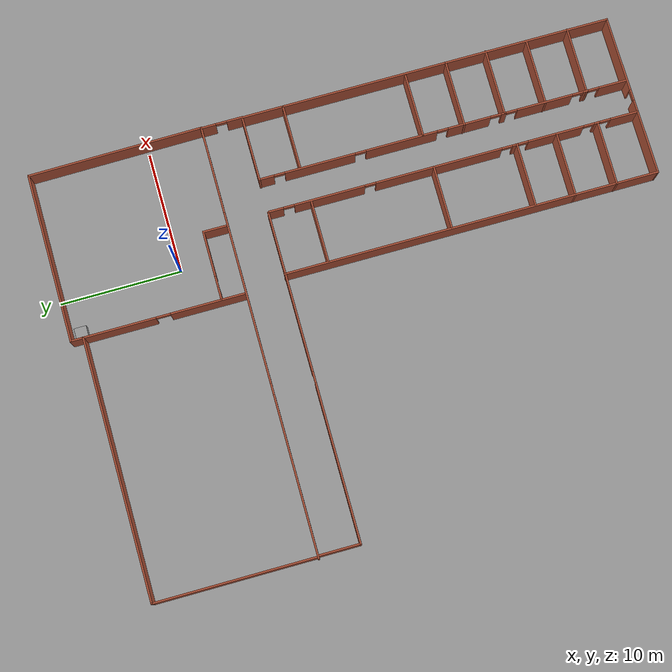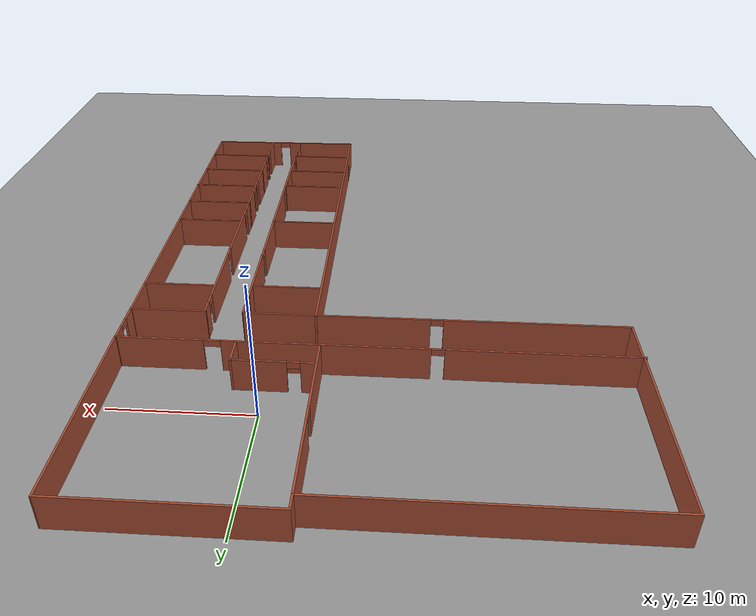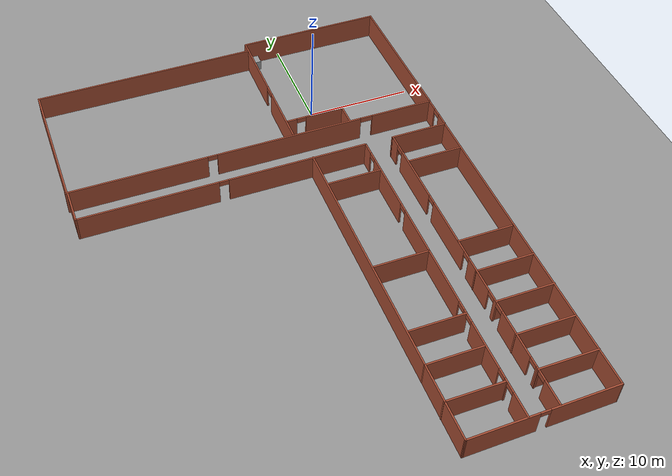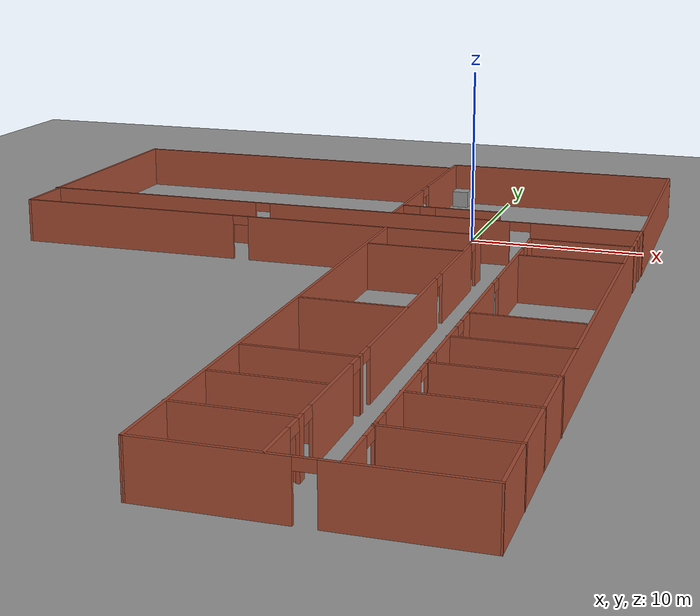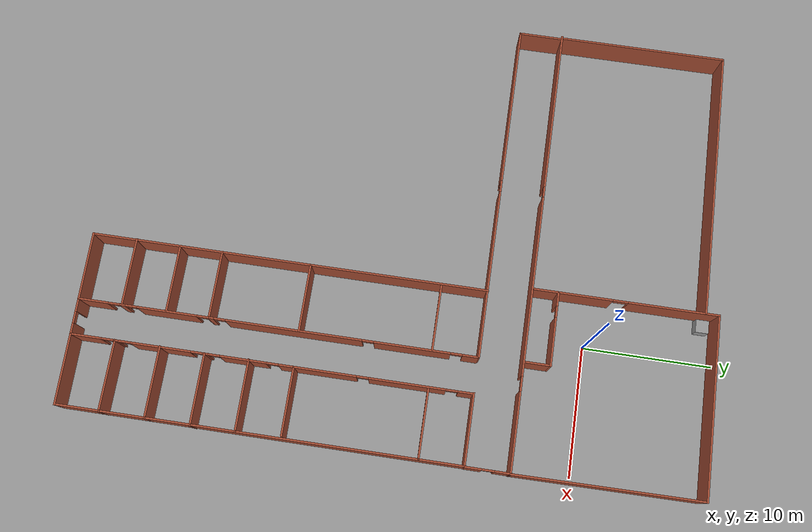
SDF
<?xml version="1.0" ?>
<sdf version='1.7'>
  <model name='fapsmap.obj'>
    <light name='sun' type='directional'>
      <cast_shadows>1</cast_shadows>
      <pose>0 0 10 0 -0 0</pose>
      <diffuse>0.8 0.8 0.8 1</diffuse>
      <specular>0.2 0.2 0.2 1</specular>
      <attenuation>
        <range>1000</range>
        <constant>0.9</constant>
        <linear>0.01</linear>
        <quadratic>0.001</quadratic>
      </attenuation>
      <direction>-0.5 0.1 -0.9</direction>
      <spot>
        <inner_angle>0</inner_angle>
        <outer_angle>0</outer_angle>
        <falloff>0</falloff>
      </spot>
    </light>
    <model name='ground_plane'>
      <static>1</static>
      <link name='link'>
        <collision name='collision'>
          <geometry>
            <plane>
              <normal>0 0 1</normal>
              <size>100 100</size>
            </plane>
          </geometry>
          <surface>
            <friction>
              <ode>
                <mu>100</mu>
                <mu2>50</mu2>
              </ode>
              <torsional>
                <ode/>
              </torsional>
            </friction>
            <contact>
              <ode/>
            </contact>
            <bounce/>
          </surface>
          <max_contacts>10</max_contacts>
        </collision>
        <visual name='visual'>
          <cast_shadows>0</cast_shadows>
          <geometry>
            <plane>
              <normal>0 0 1</normal>
              <size>100 100</size>
            </plane>
          </geometry>
          <material>
            <script>
              <uri>file://media/materials/scripts/gazebo.material</uri>
              <name>Gazebo/Grey</name>
            </script>
          </material>
        </visual>
        <self_collide>0</self_collide>
        <enable_wind>0</enable_wind>
        <kinematic>0</kinematic>
      </link>
    </model>
    <gravity>0 0 -9.8</gravity>
    <magnetic_field>6e-06 2.3e-05 -4.2e-05</magnetic_field>
    <atmosphere type='adiabatic'/>
    <physics type='ode'>
      <max_step_size>0.001</max_step_size>
      <real_time_factor>1</real_time_factor>
      <real_time_update_rate>1000</real_time_update_rate>
    </physics>
    <scene>
      <ambient>0.4 0.4 0.4 1</ambient>
      <background>0.7 0.7 0.7 1</background>
      <shadows>1</shadows>
    </scene>
    <audio>
      <device>default</device>
    </audio>
    <wind/>
    <spherical_coordinates>
      <surface_model>EARTH_WGS84</surface_model>
      <latitude_deg>0</latitude_deg>
      <longitude_deg>0</longitude_deg>
      <elevation>0</elevation>
      <heading_deg>0</heading_deg>
    </spherical_coordinates>
    <model name='fapsmap.obj'>
      <pose>-7.30116 -14.55 0 0 -0 0</pose>
      <link name='Wall_20'>
        <pose>-0.000299 9.9725 0 0 -0 3.1403</pose>
        <visual name='Wall_20_Visual_0'>
          <pose>-14.7424 0 1.25 0 -0 0</pose>
          <geometry>
            <box>
              <size>6.13838 0.15 2.5</size>
            </box>
          </geometry>
          <material>
            <script>
              <uri>file://media/materials/scripts/gazebo.material</uri>
              <name>Gazebo/Bricks</name>
            </script>
            <ambient>1 1 1 1</ambient>
          </material>
          <meta>
            <layer>0</layer>
          </meta>
        </visual>
        <collision name='Wall_20_Collision_0'>
          <geometry>
            <box>
              <size>6.13838 0.15 2.5</size>
            </box>
          </geometry>
          <pose>-14.7424 0 1.25 0 -0 0</pose>
          <max_contacts>10</max_contacts>
          <surface>
            <contact>
              <ode/>
            </contact>
            <bounce/>
            <friction>
              <torsional>
                <ode/>
              </torsional>
              <ode/>
            </friction>
          </surface>
        </collision>
        <visual name='Wall_20_Visual_1'>
          <pose>-3.4046 0 1.25 0 -0 0</pose>
          <geometry>
            <box>
              <size>14.2081 0.15 2.5</size>
            </box>
          </geometry>
          <material>
            <script>
              <uri>file://media/materials/scripts/gazebo.material</uri>
              <name>Gazebo/Bricks</name>
            </script>
            <ambient>1 1 1 1</ambient>
          </material>
          <meta>
            <layer>0</layer>
          </meta>
        </visual>
        <collision name='Wall_20_Collision_1'>
          <geometry>
            <box>
              <size>14.2081 0.15 2.5</size>
            </box>
          </geometry>
          <pose>-3.4046 0 1.25 0 -0 0</pose>
          <max_contacts>10</max_contacts>
          <surface>
            <contact>
              <ode/>
            </contact>
            <bounce/>
            <friction>
              <torsional>
                <ode/>
              </torsional>
              <ode/>
            </friction>
          </surface>
        </collision>
        <visual name='Wall_20_Visual_2'>
          <pose>11.2055 0 1.25 0 -0 0</pose>
          <geometry>
            <box>
              <size>13.2121 0.15 2.5</size>
            </box>
          </geometry>
          <material>
            <script>
              <uri>file://media/materials/scripts/gazebo.material</uri>
              <name>Gazebo/Bricks</name>
            </script>
            <ambient>1 1 1 1</ambient>
          </material>
          <meta>
            <layer>0</layer>gazebo /Home/faps/building_editor_models/fapsmap.obj

          </meta>
        </visual>
        <collision name='Wall_20_Collision_2'>
          <geometry>
            <box>
              <size>13.2121 0.15 2.5</size>
            </box>
          </geometry>
          <pose>11.2055 0 1.25 0 -0 0</pose>
          <max_contacts>10</max_contacts>
          <surface>
            <contact>
              <ode/>
            </contact>
            <bounce/>
            <friction>
              <torsional>
                <ode/>
              </torsional>
              <ode/>
            </friction>
          </surface>
        </collision>
        <visual name='Wall_20_Visual_3'>
          <pose>-11.0909 0 2.25 0 -0 0</pose>
          <geometry>
            <box>
              <size>1.16451 0.15 0.5</size>
            </box>
          </geometry>
          <material>
            <script>
              <uri>file://media/materials/scripts/gazebo.material</uri>
              <name>Gazebo/Bricks</name>
            </script>
            <ambient>1 1 1 1</ambient>
          </material>
          <meta>
            <layer>0</layer>
          </meta>
        </visual>
        <collision name='Wall_20_Collision_3'>
          <geometry>
            <box>
              <size>1.16451 0.15 0.5</size>
            </box>
          </geometry>
          <pose>-11.0909 0 2.25 0 -0 0</pose>
          <max_contacts>10</max_contacts>
          <surface>
            <contact>
              <ode/>
            </contact>
            <bounce/>
            <friction>
              <torsional>
                <ode/>
              </torsional>
              <ode/>
            </friction>
          </surface>
        </collision>
        <visual name='Wall_20_Visual_4'>
          <pose>4.14945 0 2.25 0 -0 0</pose>
          <geometry>
            <box>
              <size>0.9 0.15 0.5</size>
            </box>
          </geometry>
          <material>
            <script>
              <uri>file://media/materials/scripts/gazebo.material</uri>
              <name>Gazebo/Bricks</name>
            </script>
            <ambient>1 1 1 1</ambient>
          </material>
          <meta>
            <layer>0</layer>
          </meta>
        </visual>
        <collision name='Wall_20_Collision_4'>
          <geometry>
            <box>
              <size>0.9 0.15 0.5</size>
            </box>
          </geometry>
          <pose>4.14945 0 2.25 0 -0 0</pose>
          <max_contacts>10</max_contacts>
          <surface>
            <contact>
              <ode/>
            </contact>
            <bounce/>
            <friction>
              <torsional>
                <ode/>
              </torsional>
              <ode/>
            </friction>
          </surface>
        </collision>
        <self_collide>0</self_collide>
        <enable_wind>0</enable_wind>
        <kinematic>0</kinematic>
      </link>
      <link name='Wall_24'>
        <collision name='Wall_24_Collision'>
          <geometry>
            <box>
              <size>14.4345 0.15 2.5</size>
            </box>
          </geometry>
          <pose>0 0 1.25 0 -0 0</pose>
          <max_contacts>10</max_contacts>
          <surface>
            <contact>
              <ode/>
            </contact>
            <bounce/>
            <friction>
              <torsional>
                <ode/>
              </torsional>
              <ode/>
            </friction>
          </surface>
        </collision>
        <visual name='Wall_24_Visual'>
          <pose>0 0 1.25 0 -0 0</pose>
          <geometry>
            <box>
              <size>14.4345 0.15 2.5</size>
            </box>
          </geometry>
          <material>
            <script>
              <uri>file://media/materials/scripts/gazebo.material</uri>
              <name>Gazebo/Bricks</name>
            </script>
            <ambient>1 1 1 1</ambient>
          </material>
          <meta>
            <layer>0</layer>
          </meta>
        </visual>
        <pose>17.669 17.0915 0 0 -0 1.58022</pose>
        <self_collide>0</self_collide>
        <enable_wind>0</enable_wind>
        <kinematic>0</kinematic>
      </link>
      <link name='Wall_25'>
        <collision name='Wall_25_Collision'>
          <geometry>
            <box>
              <size>14 0.15 2.5</size>
            </box>
          </geometry>
          <pose>0 0 1.25 0 -0 0</pose>
          <max_contacts>10</max_contacts>
          <surface>
            <contact>
              <ode/>
            </contact>
            <bounce/>
            <friction>
              <torsional>
                <ode/>
              </torsional>
              <ode/>
            </friction>
          </surface>
        </collision>
        <visual name='Wall_25_Visual'>
          <pose>0 0 1.25 0 -0 0</pose>
          <geometry>
            <box>
              <size>14 0.15 2.5</size>
            </box>
          </geometry>
          <material>
            <script>
              <uri>file://media/materials/scripts/gazebo.material</uri>
              <name>Gazebo/Bricks</name>
            </script>
            <ambient>1 1 1 1</ambient>
          </material>
          <meta>
            <layer>0</layer>
          </meta>
        </visual>
        <pose>10.6767 24.2335 0 0 -0 3.14159</pose>
        <self_collide>0</self_collide>
        <enable_wind>0</enable_wind>
        <kinematic>0</kinematic>
      </link>
      <link name='Wall_26'>
        <pose>3.75167 17.1835 0 0 -0 -1.5708</pose>
        <visual name='Wall_26_Visual_0'>
          <pose>-3.62942 0 1.25 0 -0 0</pose>
          <geometry>
            <box>
              <size>6.99116 0.15 2.5</size>
            </box>
          </geometry>
          <material>
            <script>
              <uri>file://media/materials/scripts/gazebo.material</uri>
              <name>Gazebo/Bricks</name>
            </script>
            <ambient>1 1 1 1</ambient>
          </material>
          <meta>
            <layer>0</layer>
          </meta>
        </visual>
        <collision name='Wall_26_Collision_0'>
          <geometry>
            <box>
              <size>6.99116 0.15 2.5</size>
            </box>
          </geometry>
          <pose>-3.62942 0 1.25 0 -0 0</pose>
          <max_contacts>10</max_contacts>
          <surface>
            <contact>
              <ode/>
            </contact>
            <bounce/>
            <friction>
              <torsional>
                <ode/>
              </torsional>
              <ode/>
            </friction>
          </surface>
        </collision>
        <visual name='Wall_26_Visual_1'>
          <pose>4.08058 0 1.25 0 -0 0</pose>
          <geometry>
            <box>
              <size>6.08884 0.15 2.5</size>
            </box>
          </geometry>
          <material>
            <script>
              <uri>file://media/materials/scripts/gazebo.material</uri>
              <name>Gazebo/Bricks</name>
            </script>
            <ambient>1 1 1 1</ambient>
          </material>
          <meta>
            <layer>0</layer>
          </meta>
        </visual>
        <collision name='Wall_26_Collision_1'>
          <geometry>
            <box>
              <size>6.08884 0.15 2.5</size>
            </box>
          </geometry>
          <pose>4.08058 0 1.25 0 -0 0</pose>
          <max_contacts>10</max_contacts>
          <surface>
            <contact>
              <ode/>
            </contact>
            <bounce/>
            <friction>
              <torsional>
                <ode/>
              </torsional>
              <ode/>
            </friction>
          </surface>
        </collision>
        <visual name='Wall_26_Visual_2'>
          <pose>0.451159 0 2.25 0 -0 0</pose>
          <geometry>
            <box>
              <size>1.17 0.15 0.5</size>
            </box>
          </geometry>
          <material>
            <script>
              <uri>file://media/materials/scripts/gazebo.material</uri>
              <name>Gazebo/Bricks</name>
            </script>
            <ambient>1 1 1 1</ambient>
          </material>
          <meta>
            <layer>0</layer>
          </meta>
        </visual>
        <collision name='Wall_26_Collision_2'>
          <geometry>
            <box>
              <size>1.17 0.15 0.5</size>
            </box>
          </geometry>
          <pose>0.451159 0 2.25 0 -0 0</pose>
          <max_contacts>10</max_contacts>
          <surface>
            <contact>
              <ode/>
            </contact>
            <bounce/>
            <friction>
              <torsional>
                <ode/>
              </torsional>
              <ode/>
            </friction>
          </surface>
        </collision>
        <self_collide>0</self_collide>
        <enable_wind>0</enable_wind>
        <kinematic>0</kinematic>
      </link>
      <link name='Wall_28'>
        <collision name='Wall_28_Collision'>
          <geometry>
            <box>
              <size>21.5 0.15 2.5</size>
            </box>
          </geometry>
          <pose>0 0 1.25 0 -0 0</pose>
          <max_contacts>10</max_contacts>
          <surface>
            <contact>
              <ode/>
            </contact>
            <bounce/>
            <friction>
              <torsional>
                <ode/>
              </torsional>
              <ode/>
            </friction>
          </surface>
        </collision>
        <visual name='Wall_28_Visual'>
          <pose>0 0 1.25 0 -0 0</pose>
          <geometry>
            <box>
              <size>21.5 0.15 2.5</size>
            </box>
          </geometry>
          <material>
            <script>
              <uri>file://media/materials/scripts/gazebo.material</uri>
              <name>Gazebo/Bricks</name>
            </script>
            <ambient>1 1 1 1</ambient>
          </material>
          <meta>
            <layer>0</layer>
          </meta>
        </visual>
        <pose>-6.95273 23.218 0 0 -0 3.14159</pose>
        <self_collide>0</self_collide>
        <enable_wind>0</enable_wind>
        <kinematic>0</kinematic>
      </link>
      <link name='Wall_29'>
        <collision name='Wall_29_Collision'>
          <geometry>
            <box>
              <size>13.25 0.15 2.5</size>
            </box>
          </geometry>
          <pose>0 0 1.25 0 -0 0</pose>
          <max_contacts>10</max_contacts>
          <surface>
            <contact>
              <ode/>
            </contact>
            <bounce/>
            <friction>
              <torsional>
                <ode/>
              </torsional>
              <ode/>
            </friction>
          </surface>
        </collision>
        <visual name='Wall_29_Visual'>
          <pose>0 0 1.25 0 -0 0</pose>
          <geometry>
            <box>
              <size>13.25 0.15 2.5</size>
            </box>
          </geometry>
          <material>
            <script>
              <uri>file://media/materials/scripts/gazebo.material</uri>
              <name>Gazebo/Bricks</name>
            </script>
            <ambient>1 1 1 1</ambient>
          </material>
          <meta>
            <layer>0</layer>
          </meta>
        </visual>
        <pose>-17.6277 16.668 0 0 -0 -1.5708</pose>
        <self_collide>0</self_collide>
        <enable_wind>0</enable_wind>
        <kinematic>0</kinematic>
      </link>
      <link name='Wall_33'>
        <pose>17.7055 8.30531 0 0 -0 -1.5708</pose>
        <visual name='Wall_33_Visual_0'>
          <pose>-1.0981 0 1.25 0 -0 0</pose>
          <geometry>
            <box>
              <size>1.30381 0.15 2.5</size>
            </box>
          </geometry>
          <material>
            <script>
              <uri>file://media/materials/scripts/gazebo.material</uri>
              <name>Gazebo/Bricks</name>
            </script>
            <ambient>1 1 1 1</ambient>
          </material>
          <meta>
            <layer>0</layer>
          </meta>
        </visual>
        <collision name='Wall_33_Collision_0'>
          <geometry>
            <box>
              <size>1.30381 0.15 2.5</size>
            </box>
          </geometry>
          <pose>-1.0981 0 1.25 0 -0 0</pose>
          <max_contacts>10</max_contacts>
          <surface>
            <contact>
              <ode/>
            </contact>
            <bounce/>
            <friction>
              <torsional>
                <ode/>
              </torsional>
              <ode/>
            </friction>
          </surface>
        </collision>
        <visual name='Wall_33_Visual_1'>
          <pose>1.1019 0 1.25 0 -0 0</pose>
          <geometry>
            <box>
              <size>1.29619 0.15 2.5</size>
            </box>
          </geometry>
          <material>
            <script>
              <uri>file://media/materials/scripts/gazebo.material</uri>
              <name>Gazebo/Bricks</name>
            </script>
            <ambient>1 1 1 1</ambient>
          </material>
          <meta>
            <layer>0</layer>
          </meta>
        </visual>
        <collision name='Wall_33_Collision_1'>
          <geometry>
            <box>
              <size>1.29619 0.15 2.5</size>
            </box>
          </geometry>
          <pose>1.1019 0 1.25 0 -0 0</pose>
          <max_contacts>10</max_contacts>
          <surface>
            <contact>
              <ode/>
            </contact>
            <bounce/>
            <friction>
              <torsional>
                <ode/>
              </torsional>
              <ode/>
            </friction>
          </surface>
        </collision>
        <visual name='Wall_33_Visual_2'>
          <pose>0.003805 0 2.25 0 -0 0</pose>
          <geometry>
            <box>
              <size>0.9 0.15 0.5</size>
            </box>
          </geometry>
          <material>
            <script>
              <uri>file://media/materials/scripts/gazebo.material</uri>
              <name>Gazebo/Bricks</name>
            </script>
            <ambient>1 1 1 1</ambient>
          </material>
          <meta>
            <layer>0</layer>
          </meta>
        </visual>
        <collision name='Wall_33_Collision_2'>
          <geometry>
            <box>
              <size>0.9 0.15 0.5</size>
            </box>
          </geometry>
          <pose>0.003805 0 2.25 0 -0 0</pose>
          <max_contacts>10</max_contacts>
          <surface>
            <contact>
              <ode/>
            </contact>
            <bounce/>
            <friction>
              <torsional>
                <ode/>
              </torsional>
              <ode/>
            </friction>
          </surface>
        </collision>
        <self_collide>0</self_collide>
        <enable_wind>0</enable_wind>
        <kinematic>0</kinematic>
      </link>
      <link name='Wall_39'>
        <collision name='Wall_39_Collision'>
          <geometry>
            <box>
              <size>5.5 0.15 2.5</size>
            </box>
          </geometry>
          <pose>0 0 1.25 0 -0 0</pose>
          <max_contacts>10</max_contacts>
          <surface>
            <contact>
              <ode/>
            </contact>
            <bounce/>
            <friction>
              <torsional>
                <ode/>
              </torsional>
              <ode/>
            </friction>
          </surface>
        </collision>
        <visual name='Wall_39_Visual'>
          <pose>0 0 1.25 0 -0 0</pose>
          <geometry>
            <box>
              <size>5.5 0.15 2.5</size>
            </box>
          </geometry>
          <material>
            <script>
              <uri>file://media/materials/scripts/gazebo.material</uri>
              <name>Gazebo/Bricks</name>
            </script>
            <ambient>1 1 1 1</ambient>
          </material>
          <meta>
            <layer>0</layer>
          </meta>
        </visual>
        <pose>15.0039 6.56104 0 0 -0 0</pose>
        <self_collide>0</self_collide>
        <enable_wind>0</enable_wind>
        <kinematic>0</kinematic>
      </link>
      <link name='Wall_41'>
        <pose>-4.00364 6.5805 0 0 -0 3.14159</pose>
        <visual name='Wall_41_Visual_0'>
          <pose>-6.97405 0 1.25 0 -0 0</pose>
          <geometry>
            <box>
              <size>13.3019 0.15 2.5</size>
            </box>
          </geometry>
          <material>
            <script>
              <uri>file://media/materials/scripts/gazebo.material</uri>
              <name>Gazebo/Bricks</name>
            </script>
            <ambient>1 1 1 1</ambient>
          </material>
          <meta>
            <layer>0</layer>
          </meta>
        </visual>
        <collision name='Wall_41_Collision_0'>
          <geometry>
            <box>
              <size>13.3019 0.15 2.5</size>
            </box>
          </geometry>
          <pose>-6.97405 0 1.25 0 -0 0</pose>
          <max_contacts>10</max_contacts>
          <surface>
            <contact>
              <ode/>
            </contact>
            <bounce/>
            <friction>
              <torsional>
                <ode/>
              </torsional>
              <ode/>
            </friction>
          </surface>
        </collision>
        <visual name='Wall_41_Visual_1'>
          <pose>7.10095 0 1.25 0 -0 0</pose>
          <geometry>
            <box>
              <size>13.0481 0.15 2.5</size>
            </box>
          </geometry>
          <material>
            <script>
              <uri>file://media/materials/scripts/gazebo.material</uri>
              <name>Gazebo/Bricks</name>
            </script>
            <ambient>1 1 1 1</ambient>
          </material>
          <meta>
            <layer>0</layer>
          </meta>
        </visual>
        <collision name='Wall_41_Collision_1'>
          <geometry>
            <box>
              <size>13.0481 0.15 2.5</size>
            </box>
          </geometry>
          <pose>7.10095 0 1.25 0 -0 0</pose>
          <max_contacts>10</max_contacts>
          <surface>
            <contact>
              <ode/>
            </contact>
            <bounce/>
            <friction>
              <torsional>
                <ode/>
              </torsional>
              <ode/>
            </friction>
          </surface>
        </collision>
        <visual name='Wall_41_Visual_2'>
          <pose>0.126898 0 2.25 0 -0 0</pose>
          <geometry>
            <box>
              <size>0.9 0.15 0.5</size>
            </box>
          </geometry>
          <material>
            <script>
              <uri>file://media/materials/scripts/gazebo.material</uri>
              <name>Gazebo/Bricks</name>
            </script>
            <ambient>1 1 1 1</ambient>
          </material>
          <meta>
            <layer>0</layer>
          </meta>
        </visual>
        <collision name='Wall_41_Collision_2'>
          <geometry>
            <box>
              <size>0.9 0.15 0.5</size>
            </box>
          </geometry>
          <pose>0.126898 0 2.25 0 -0 0</pose>
          <max_contacts>10</max_contacts>
          <surface>
            <contact>
              <ode/>
            </contact>
            <bounce/>
            <friction>
              <torsional>
                <ode/>
              </torsional>
              <ode/>
            </friction>
          </surface>
        </collision>
        <self_collide>0</self_collide>
        <enable_wind>0</enable_wind>
        <kinematic>0</kinematic>
      </link>
      <link name='Wall_42'>
        <collision name='Wall_42_Collision'>
          <geometry>
            <box>
              <size>3.5 0.15 2.5</size>
            </box>
          </geometry>
          <pose>0 0 1.25 0 -0 0</pose>
          <max_contacts>10</max_contacts>
          <surface>
            <contact>
              <ode/>
            </contact>
            <bounce/>
            <friction>
              <torsional>
                <ode/>
              </torsional>
              <ode/>
            </friction>
          </surface>
        </collision>
        <visual name='Wall_42_Visual'>
          <pose>0 0 1.25 0 -0 0</pose>
          <geometry>
            <box>
              <size>3.5 0.15 2.5</size>
            </box>
          </geometry>
          <material>
            <script>
              <uri>file://media/materials/scripts/gazebo.material</uri>
              <name>Gazebo/Bricks</name>
            </script>
            <ambient>1 1 1 1</ambient>
          </material>
          <meta>
            <layer>0</layer>
          </meta>
        </visual>
        <pose>-17.5536 8.2555 0 0 -0 1.5708</pose>
        <self_collide>0</self_collide>
        <enable_wind>0</enable_wind>
        <kinematic>0</kinematic>
      </link>
      <link name='Wall_44'>
        <pose>12.3594 -8.7985 0 0 -0 -1.5708</pose>
        <visual name='Wall_44_Visual_0'>
          <pose>-14.7698 0 1.25 0 -0 0</pose>
          <geometry>
            <box>
              <size>1.21049 0.15 2.5</size>
            </box>
          </geometry>
          <material>
            <script>
              <uri>file://media/materials/scripts/gazebo.material</uri>
              <name>Gazebo/Bricks</name>
            </script>
            <ambient>1 1 1 1</ambient>
          </material>
          <meta>
            <layer>0</layer>
          </meta>
        </visual>
        <collision name='Wall_44_Collision_0'>
          <geometry>
            <box>
              <size>1.21049 0.15 2.5</size>
            </box>
          </geometry>
          <pose>-14.7698 0 1.25 0 -0 0</pose>
          <max_contacts>10</max_contacts>
          <surface>
            <contact>
              <ode/>
            </contact>
            <bounce/>
            <friction>
              <torsional>
                <ode/>
              </torsional>
              <ode/>
            </friction>
          </surface>
        </collision>
        <visual name='Wall_44_Visual_1'>
          <pose>-10.3459 0 1.25 0 -0 0</pose>
          <geometry>
            <box>
              <size>5.8373 0.15 2.5</size>
            </box>
          </geometry>
          <material>
            <script>
              <uri>file://media/materials/scripts/gazebo.material</uri>
              <name>Gazebo/Bricks</name>
            </script>
            <ambient>1 1 1 1</ambient>
          </material>
          <meta>
            <layer>0</layer>
          </meta>
        </visual>
        <collision name='Wall_44_Collision_1'>
          <geometry>
            <box>
              <size>5.8373 0.15 2.5</size>
            </box>
          </geometry>
          <pose>-10.3459 0 1.25 0 -0 0</pose>
          <max_contacts>10</max_contacts>
          <surface>
            <contact>
              <ode/>
            </contact>
            <bounce/>
            <friction>
              <torsional>
                <ode/>
              </torsional>
              <ode/>
            </friction>
          </surface>
        </collision>
        <visual name='Wall_44_Visual_2'>
          <pose>-3.56241 0 1.25 0 -0 0</pose>
          <geometry>
            <box>
              <size>5.92959 0.15 2.5</size>
            </box>
          </geometry>
          <material>
            <script>
              <uri>file://media/materials/scripts/gazebo.material</uri>
              <name>Gazebo/Bricks</name>
            </script>
            <ambient>1 1 1 1</ambient>
          </material>
          <meta>
            <layer>0</layer>
          </meta>
        </visual>
        <collision name='Wall_44_Collision_2'>
          <geometry>
            <box>
              <size>5.92959 0.15 2.5</size>
            </box>
          </geometry>
          <pose>-3.56241 0 1.25 0 -0 0</pose>
          <max_contacts>10</max_contacts>
          <surface>
            <contact>
              <ode/>
            </contact>
            <bounce/>
            <friction>
              <torsional>
                <ode/>
              </torsional>
              <ode/>
            </friction>
          </surface>
        </collision>
        <visual name='Wall_44_Visual_3'>
          <pose>2.08277 0 1.25 0 -0 0</pose>
          <geometry>
            <box>
              <size>3.56077 0.15 2.5</size>
            </box>
          </geometry>
          <material>
            <script>
              <uri>file://media/materials/scripts/gazebo.material</uri>
              <name>Gazebo/Bricks</name>
            </script>
            <ambient>1 1 1 1</ambient>
          </material>
          <meta>
            <layer>0</layer>
          </meta>
        </visual>
        <collision name='Wall_44_Collision_3'>
          <geometry>
            <box>
              <size>3.56077 0.15 2.5</size>
            </box>
          </geometry>
          <pose>2.08277 0 1.25 0 -0 0</pose>
          <max_contacts>10</max_contacts>
          <surface>
            <contact>
              <ode/>
            </contact>
            <bounce/>
            <friction>
              <torsional>
                <ode/>
              </torsional>
              <ode/>
            </friction>
          </surface>
        </collision>
        <visual name='Wall_44_Visual_4'>
          <pose>4.97458 0 1.25 0 -0 0</pose>
          <geometry>
            <box>
              <size>0.422849 0.15 2.5</size>
            </box>
          </geometry>
          <material>
            <script>
              <uri>file://media/materials/scripts/gazebo.material</uri>
              <name>Gazebo/Bricks</name>
            </script>
            <ambient>1 1 1 1</ambient>
          </material>
          <meta>
            <layer>0</layer>
          </meta>
        </visual>
        <collision name='Wall_44_Collision_4'>
          <geometry>
            <box>
              <size>0.422849 0.15 2.5</size>
            </box>
          </geometry>
          <pose>4.97458 0 1.25 0 -0 0</pose>
          <max_contacts>10</max_contacts>
          <surface>
            <contact>
              <ode/>
            </contact>
            <bounce/>
            <friction>
              <torsional>
                <ode/>
              </torsional>
              <ode/>
            </friction>
          </surface>
        </collision>
        <visual name='Wall_44_Visual_5'>
          <pose>8.40476 0 1.25 0 -0 0</pose>
          <geometry>
            <box>
              <size>4.63751 0.15 2.5</size>
            </box>
          </geometry>
          <material>
            <script>
              <uri>file://media/materials/scripts/gazebo.material</uri>
              <name>Gazebo/Bricks</name>
            </script>
            <ambient>1 1 1 1</ambient>
          </material>
          <meta>
            <layer>0</layer>
          </meta>
        </visual>
        <collision name='Wall_44_Collision_5'>
          <geometry>
            <box>
              <size>4.63751 0.15 2.5</size>
            </box>
          </geometry>
          <pose>8.40476 0 1.25 0 -0 0</pose>
          <max_contacts>10</max_contacts>
          <surface>
            <contact>
              <ode/>
            </contact>
            <bounce/>
            <friction>
              <torsional>
                <ode/>
              </torsional>
              <ode/>
            </friction>
          </surface>
        </collision>
        <visual name='Wall_44_Visual_6'>
          <pose>11.8349 0 1.25 0 -0 0</pose>
          <geometry>
            <box>
              <size>0.422849 0.15 2.5</size>
            </box>
          </geometry>
          <material>
            <script>
              <uri>file://media/materials/scripts/gazebo.material</uri>
              <name>Gazebo/Bricks</name>
            </script>
            <ambient>1 1 1 1</ambient>
          </material>
          <meta>
            <layer>0</layer>
          </meta>
        </visual>
        <collision name='Wall_44_Collision_6'>
          <geometry>
            <box>
              <size>0.422849 0.15 2.5</size>
            </box>
          </geometry>
          <pose>11.8349 0 1.25 0 -0 0</pose>
          <max_contacts>10</max_contacts>
          <surface>
            <contact>
              <ode/>
            </contact>
            <bounce/>
            <friction>
              <torsional>
                <ode/>
              </torsional>
              <ode/>
            </friction>
          </surface>
        </collision>
        <visual name='Wall_44_Visual_7'>
          <pose>14.1607 0 1.25 0 -0 0</pose>
          <geometry>
            <box>
              <size>2.42863 0.15 2.5</size>
            </box>
          </geometry>
          <material>
            <script>
              <uri>file://media/materials/scripts/gazebo.material</uri>
              <name>Gazebo/Bricks</name>
            </script>
            <ambient>1 1 1 1</ambient>
          </material>
          <meta>
            <layer>0</layer>
          </meta>
        </visual>
        <collision name='Wall_44_Collision_7'>
          <geometry>
            <box>
              <size>2.42863 0.15 2.5</size>
            </box>
          </geometry>
          <pose>14.1607 0 1.25 0 -0 0</pose>
          <max_contacts>10</max_contacts>
          <surface>
            <contact>
              <ode/>
            </contact>
            <bounce/>
            <friction>
              <torsional>
                <ode/>
              </torsional>
              <ode/>
            </friction>
          </surface>
        </collision>
        <visual name='Wall_44_Visual_8'>
          <pose>-13.7145 0 2.25 0 -0 0</pose>
          <geometry>
            <box>
              <size>0.9 0.15 0.5</size>
            </box>
          </geometry>
          <material>
            <script>
              <uri>file://media/materials/scripts/gazebo.material</uri>
              <name>Gazebo/Bricks</name>
            </script>
            <ambient>1 1 1 1</ambient>
          </material>
          <meta>
            <layer>0</layer>
          </meta>
        </visual>
        <collision name='Wall_44_Collision_8'>
          <geometry>
            <box>
              <size>0.9 0.15 0.5</size>
            </box>
          </geometry>
          <pose>-13.7145 0 2.25 0 -0 0</pose>
          <max_contacts>10</max_contacts>
          <surface>
            <contact>
              <ode/>
            </contact>
            <bounce/>
            <friction>
              <torsional>
                <ode/>
              </torsional>
              <ode/>
            </friction>
          </surface>
        </collision>
        <visual name='Wall_44_Visual_9'>
          <pose>-6.97721 0 2.25 0 -0 0</pose>
          <geometry>
            <box>
              <size>0.9 0.15 0.5</size>
            </box>
          </geometry>
          <material>
            <script>
              <uri>file://media/materials/scripts/gazebo.material</uri>
              <name>Gazebo/Bricks</name>
            </script>
            <ambient>1 1 1 1</ambient>
          </material>
          <meta>
            <layer>0</layer>
          </meta>
        </visual>
        <collision name='Wall_44_Collision_9'>
          <geometry>
            <box>
              <size>0.9 0.15 0.5</size>
            </box>
          </geometry>
          <pose>-6.97721 0 2.25 0 -0 0</pose>
          <max_contacts>10</max_contacts>
          <surface>
            <contact>
              <ode/>
            </contact>
            <bounce/>
            <friction>
              <torsional>
                <ode/>
              </torsional>
              <ode/>
            </friction>
          </surface>
        </collision>
        <visual name='Wall_44_Visual_10'>
          <pose>-0.147614 0 2.25 0 -0 0</pose>
          <geometry>
            <box>
              <size>0.9 0.15 0.5</size>
            </box>
          </geometry>
          <material>
            <script>
              <uri>file://media/materials/scripts/gazebo.material</uri>
              <name>Gazebo/Bricks</name>
            </script>
            <ambient>1 1 1 1</ambient>
          </material>
          <meta>
            <layer>0</layer>
          </meta>
        </visual>
        <collision name='Wall_44_Collision_10'>
          <geometry>
            <box>
              <size>0.9 0.15 0.5</size>
            </box>
          </geometry>
          <pose>-0.147614 0 2.25 0 -0 0</pose>
          <max_contacts>10</max_contacts>
          <surface>
            <contact>
              <ode/>
            </contact>
            <bounce/>
            <friction>
              <torsional>
                <ode/>
              </torsional>
              <ode/>
            </friction>
          </surface>
        </collision>
        <visual name='Wall_44_Visual_11'>
          <pose>4.31316 0 2.25 0 -0 0</pose>
          <geometry>
            <box>
              <size>0.9 0.15 0.5</size>
            </box>
          </geometry>
          <material>
            <script>
              <uri>file://media/materials/scripts/gazebo.material</uri>
              <name>Gazebo/Bricks</name>
            </script>
            <ambient>1 1 1 1</ambient>
          </material>
          <meta>
            <layer>0</layer>
          </meta>
        </visual>
        <collision name='Wall_44_Collision_11'>
          <geometry>
            <box>
              <size>0.9 0.15 0.5</size>
            </box>
          </geometry>
          <pose>4.31316 0 2.25 0 -0 0</pose>
          <max_contacts>10</max_contacts>
          <surface>
            <contact>
              <ode/>
            </contact>
            <bounce/>
            <friction>
              <torsional>
                <ode/>
              </torsional>
              <ode/>
            </friction>
          </surface>
        </collision>
        <visual name='Wall_44_Visual_12'>
          <pose>5.63601 0 2.25 0 -0 0</pose>
          <geometry>
            <box>
              <size>0.9 0.15 0.5</size>
            </box>
          </geometry>
          <material>
            <script>
              <uri>file://media/materials/scripts/gazebo.material</uri>
              <name>Gazebo/Bricks</name>
            </script>
            <ambient>1 1 1 1</ambient>
          </material>
          <meta>
            <layer>0</layer>
          </meta>
        </visual>
        <collision name='Wall_44_Collision_12'>
          <geometry>
            <box>
              <size>0.9 0.15 0.5</size>
            </box>
          </geometry>
          <pose>5.63601 0 2.25 0 -0 0</pose>
          <max_contacts>10</max_contacts>
          <surface>
            <contact>
              <ode/>
            </contact>
            <bounce/>
            <friction>
              <torsional>
                <ode/>
              </torsional>
              <ode/>
            </friction>
          </surface>
        </collision>
        <visual name='Wall_44_Visual_13'>
          <pose>11.1735 0 2.25 0 -0 0</pose>
          <geometry>
            <box>
              <size>0.9 0.15 0.5</size>
            </box>
          </geometry>
          <material>
            <script>
              <uri>file://media/materials/scripts/gazebo.material</uri>
              <name>Gazebo/Bricks</name>
            </script>
            <ambient>1 1 1 1</ambient>
          </material>
          <meta>
            <layer>0</layer>
          </meta>
        </visual>
        <collision name='Wall_44_Collision_13'>
          <geometry>
            <box>
              <size>0.9 0.15 0.5</size>
            </box>
          </geometry>
          <pose>11.1735 0 2.25 0 -0 0</pose>
          <max_contacts>10</max_contacts>
          <surface>
            <contact>
              <ode/>
            </contact>
            <bounce/>
            <friction>
              <torsional>
                <ode/>
              </torsional>
              <ode/>
            </friction>
          </surface>
        </collision>
        <visual name='Wall_44_Visual_14'>
          <pose>12.4964 0 2.25 0 -0 0</pose>
          <geometry>
            <box>
              <size>0.9 0.15 0.5</size>
            </box>
          </geometry>
          <material>
            <script>
              <uri>file://media/materials/scripts/gazebo.material</uri>
              <name>Gazebo/Bricks</name>
            </script>
            <ambient>1 1 1 1</ambient>
          </material>
          <meta>
            <layer>0</layer>
          </meta>
        </visual>
        <collision name='Wall_44_Collision_14'>
          <geometry>
            <box>
              <size>0.9 0.15 0.5</size>
            </box>
          </geometry>
          <pose>12.4964 0 2.25 0 -0 0</pose>
          <max_contacts>10</max_contacts>
          <surface>
            <contact>
              <ode/>
            </contact>
            <bounce/>
            <friction>
              <torsional>
                <ode/>
              </torsional>
              <ode/>
            </friction>
          </surface>
        </collision>
        <self_collide>0</self_collide>
        <enable_wind>0</enable_wind>
        <kinematic>0</kinematic>
      </link>
      <link name='Wall_47'>
        <pose>9.60614 -8.80383 0 0 -0 -1.5708</pose>
        <visual name='Wall_47_Visual_0'>
          <pose>-14.757 0 1.25 0 -0 0</pose>
          <geometry>
            <box>
              <size>1.23592 0.15 2.5</size>
            </box>
          </geometry>
          <material>
            <script>
              <uri>file://media/materials/scripts/gazebo.material</uri>
              <name>Gazebo/Bricks</name>
            </script>
            <ambient>1 1 1 1</ambient>
          </material>
          <meta>
            <layer>0</layer>
          </meta>
        </visual>
        <collision name='Wall_47_Collision_0'>
          <geometry>
            <box>
              <size>1.23592 0.15 2.5</size>
            </box>
          </geometry>
          <pose>-14.757 0 1.25 0 -0 0</pose>
          <max_contacts>10</max_contacts>
          <surface>
            <contact>
              <ode/>
            </contact>
            <bounce/>
            <friction>
              <torsional>
                <ode/>
              </torsional>
              <ode/>
            </friction>
          </surface>
        </collision>
        <visual name='Wall_47_Visual_1'>
          <pose>-10.3204 0 1.25 0 -0 0</pose>
          <geometry>
            <box>
              <size>5.8373 0.15 2.5</size>
            </box>
          </geometry>
          <material>
            <script>
              <uri>file://media/materials/scripts/gazebo.material</uri>
              <name>Gazebo/Bricks</name>
            </script>
            <ambient>1 1 1 1</ambient>
          </material>
          <meta>
            <layer>0</layer>
          </meta>
        </visual>
        <collision name='Wall_47_Collision_1'>
          <geometry>
            <box>
              <size>5.8373 0.15 2.5</size>
            </box>
          </geometry>
          <pose>-10.3204 0 1.25 0 -0 0</pose>
          <max_contacts>10</max_contacts>
          <surface>
            <contact>
              <ode/>
            </contact>
            <bounce/>
            <friction>
              <torsional>
                <ode/>
              </torsional>
              <ode/>
            </friction>
          </surface>
        </collision>
        <visual name='Wall_47_Visual_2'>
          <pose>-1.26045 0 1.25 0 -0 0</pose>
          <geometry>
            <box>
              <size>10.4827 0.15 2.5</size>
            </box>
          </geometry>
          <material>
            <script>
              <uri>file://media/materials/scripts/gazebo.material</uri>
              <name>Gazebo/Bricks</name>
            </script>
            <ambient>1 1 1 1</ambient>
          </material>
          <meta>
            <layer>0</layer>
          </meta>
        </visual>
        <collision name='Wall_47_Collision_2'>
          <geometry>
            <box>
              <size>10.4827 0.15 2.5</size>
            </box>
          </geometry>
          <pose>-1.26045 0 1.25 0 -0 0</pose>
          <max_contacts>10</max_contacts>
          <surface>
            <contact>
              <ode/>
            </contact>
            <bounce/>
            <friction>
              <torsional>
                <ode/>
              </torsional>
              <ode/>
            </friction>
          </surface>
        </collision>
        <visual name='Wall_47_Visual_3'>
          <pose>5.07693 0 1.25 0 -0 0</pose>
          <geometry>
            <box>
              <size>0.392085 0.15 2.5</size>
            </box>
          </geometry>
          <material>
            <script>
              <uri>file://media/materials/scripts/gazebo.material</uri>
              <name>Gazebo/Bricks</name>
            </script>
            <ambient>1 1 1 1</ambient>
          </material>
          <meta>
            <layer>0</layer>
          </meta>
        </visual>
        <collision name='Wall_47_Collision_3'>
          <geometry>
            <box>
              <size>0.392085 0.15 2.5</size>
            </box>
          </geometry>
          <pose>5.07693 0 1.25 0 -0 0</pose>
          <max_contacts>10</max_contacts>
          <surface>
            <contact>
              <ode/>
            </contact>
            <bounce/>
            <friction>
              <torsional>
                <ode/>
              </torsional>
              <ode/>
            </friction>
          </surface>
        </collision>
        <visual name='Wall_47_Visual_4'>
          <pose>8.49172 0 1.25 0 -0 0</pose>
          <geometry>
            <box>
              <size>4.63751 0.15 2.5</size>
            </box>
          </geometry>
          <material>
            <script>
              <uri>file://media/materials/scripts/gazebo.material</uri>
              <name>Gazebo/Bricks</name>
            </script>
            <ambient>1 1 1 1</ambient>
          </material>
          <meta>
            <layer>0</layer>
          </meta>
        </visual>
        <collision name='Wall_47_Collision_4'>
          <geometry>
            <box>
              <size>4.63751 0.15 2.5</size>
            </box>
          </geometry>
          <pose>8.49172 0 1.25 0 -0 0</pose>
          <max_contacts>10</max_contacts>
          <surface>
            <contact>
              <ode/>
            </contact>
            <bounce/>
            <friction>
              <torsional>
                <ode/>
              </torsional>
              <ode/>
            </friction>
          </surface>
        </collision>
        <visual name='Wall_47_Visual_5'>
          <pose>11.9373 0 1.25 0 -0 0</pose>
          <geometry>
            <box>
              <size>0.453613 0.15 2.5</size>
            </box>
          </geometry>
          <material>
            <script>
              <uri>file://media/materials/scripts/gazebo.material</uri>
              <name>Gazebo/Bricks</name>
            </script>
            <ambient>1 1 1 1</ambient>
          </material>
          <meta>
            <layer>0</layer>
          </meta>
        </visual>
        <collision name='Wall_47_Collision_5'>
          <geometry>
            <box>
              <size>0.453613 0.15 2.5</size>
            </box>
          </geometry>
          <pose>11.9373 0 1.25 0 -0 0</pose>
          <max_contacts>10</max_contacts>
          <surface>
            <contact>
              <ode/>
            </contact>
            <bounce/>
            <friction>
              <torsional>
                <ode/>
              </torsional>
              <ode/>
            </friction>
          </surface>
        </collision>
        <visual name='Wall_47_Visual_6'>
          <pose>14.2195 0 1.25 0 -0 0</pose>
          <geometry>
            <box>
              <size>2.31091 0.15 2.5</size>
            </box>
          </geometry>
          <material>
            <script>
              <uri>file://media/materials/scripts/gazebo.material</uri>
              <name>Gazebo/Bricks</name>
            </script>
            <ambient>1 1 1 1</ambient>
          </material>
          <meta>
            <layer>0</layer>
          </meta>
        </visual>
        <collision name='Wall_47_Collision_6'>
          <geometry>
            <box>
              <size>2.31091 0.15 2.5</size>
            </box>
          </geometry>
          <pose>14.2195 0 1.25 0 -0 0</pose>
          <max_contacts>10</max_contacts>
          <surface>
            <contact>
              <ode/>
            </contact>
            <bounce/>
            <friction>
              <torsional>
                <ode/>
              </torsional>
              <ode/>
            </friction>
          </surface>
        </collision>
        <visual name='Wall_47_Visual_7'>
          <pose>-13.6891 0 2.25 0 -0 0</pose>
          <geometry>
            <box>
              <size>0.9 0.15 0.5</size>
            </box>
          </geometry>
          <material>
            <script>
              <uri>file://media/materials/scripts/gazebo.material</uri>
              <name>Gazebo/Bricks</name>
            </script>
            <ambient>1 1 1 1</ambient>
          </material>
          <meta>
            <layer>0</layer>
          </meta>
        </visual>
        <collision name='Wall_47_Collision_7'>
          <geometry>
            <box>
              <size>0.9 0.15 0.5</size>
            </box>
          </geometry>
          <pose>-13.6891 0 2.25 0 -0 0</pose>
          <max_contacts>10</max_contacts>
          <surface>
            <contact>
              <ode/>
            </contact>
            <bounce/>
            <friction>
              <torsional>
                <ode/>
              </torsional>
              <ode/>
            </friction>
          </surface>
        </collision>
        <visual name='Wall_47_Visual_8'>
          <pose>-6.95177 0 2.25 0 -0 0</pose>
          <geometry>
            <box>
              <size>0.9 0.15 0.5</size>
            </box>
          </geometry>
          <material>
            <script>
              <uri>file://media/materials/scripts/gazebo.material</uri>
              <name>Gazebo/Bricks</name>
            </script>
            <ambient>1 1 1 1</ambient>
          </material>
          <meta>
            <layer>0</layer>
          </meta>
        </visual>
        <collision name='Wall_47_Collision_8'>
          <geometry>
            <box>
              <size>0.9 0.15 0.5</size>
            </box>
          </geometry>
          <pose>-6.95177 0 2.25 0 -0 0</pose>
          <max_contacts>10</max_contacts>
          <surface>
            <contact>
              <ode/>
            </contact>
            <bounce/>
            <friction>
              <torsional>
                <ode/>
              </torsional>
              <ode/>
            </friction>
          </surface>
        </collision>
        <visual name='Wall_47_Visual_9'>
          <pose>4.43088 0 2.25 0 -0 0</pose>
          <geometry>
            <box>
              <size>0.9 0.15 0.5</size>
            </box>
          </geometry>
          <material>
            <script>
              <uri>file://media/materials/scripts/gazebo.material</uri>
              <name>Gazebo/Bricks</name>
            </script>
            <ambient>1 1 1 1</ambient>
          </material>
          <meta>
            <layer>0</layer>
          </meta>
        </visual>
        <collision name='Wall_47_Collision_9'>
          <geometry>
            <box>
              <size>0.9 0.15 0.5</size>
            </box>
          </geometry>
          <pose>4.43088 0 2.25 0 -0 0</pose>
          <max_contacts>10</max_contacts>
          <surface>
            <contact>
              <ode/>
            </contact>
            <bounce/>
            <friction>
              <torsional>
                <ode/>
              </torsional>
              <ode/>
            </friction>
          </surface>
        </collision>
        <visual name='Wall_47_Visual_10'>
          <pose>5.72297 0 2.25 0 -0 0</pose>
          <geometry>
            <box>
              <size>0.9 0.15 0.5</size>
            </box>
          </geometry>
          <material>
            <script>
              <uri>file://media/materials/scripts/gazebo.material</uri>
              <name>Gazebo/Bricks</name>
            </script>
            <ambient>1 1 1 1</ambient>
          </material>
          <meta>
            <layer>0</layer>
          </meta>
        </visual>
        <collision name='Wall_47_Collision_10'>
          <geometry>
            <box>
              <size>0.9 0.15 0.5</size>
            </box>
          </geometry>
          <pose>5.72297 0 2.25 0 -0 0</pose>
          <max_contacts>10</max_contacts>
          <surface>
            <contact>
              <ode/>
            </contact>
            <bounce/>
            <friction>
              <torsional>
                <ode/>
              </torsional>
              <ode/>
            </friction>
          </surface>
        </collision>
        <visual name='Wall_47_Visual_11'>
          <pose>11.2605 0 2.25 0 -0 0</pose>
          <geometry>
            <box>
              <size>0.9 0.15 0.5</size>
            </box>
          </geometry>
          <material>
            <script>
              <uri>file://media/materials/scripts/gazebo.material</uri>
              <name>Gazebo/Bricks</name>
            </script>
            <ambient>1 1 1 1</ambient>
          </material>
          <meta>
            <layer>0</layer>
          </meta>
        </visual>
        <collision name='Wall_47_Collision_11'>
          <geometry>
            <box>
              <size>0.9 0.15 0.5</size>
            </box>
          </geometry>
          <pose>11.2605 0 2.25 0 -0 0</pose>
          <max_contacts>10</max_contacts>
          <surface>
            <contact>
              <ode/>
            </contact>
            <bounce/>
            <friction>
              <torsional>
                <ode/>
              </torsional>
              <ode/>
            </friction>
          </surface>
        </collision>
        <visual name='Wall_47_Visual_12'>
          <pose>12.6141 0 2.25 0 -0 0</pose>
          <geometry>
            <box>
              <size>0.9 0.15 0.5</size>
            </box>
          </geometry>
          <material>
            <script>
              <uri>file://media/materials/scripts/gazebo.material</uri>
              <name>Gazebo/Bricks</name>
            </script>
            <ambient>1 1 1 1</ambient>
          </material>
          <meta>
            <layer>0</layer>
          </meta>
        </visual>
        <collision name='Wall_47_Collision_12'>
          <geometry>
            <box>
              <size>0.9 0.15 0.5</size>
            </box>
          </geometry>
          <pose>12.6141 0 2.25 0 -0 0</pose>
          <max_contacts>10</max_contacts>
          <surface>
            <contact>
              <ode/>
            </contact>
            <bounce/>
            <friction>
              <torsional>
                <ode/>
              </torsional>
              <ode/>
            </friction>
          </surface>
        </collision>
        <self_collide>0</self_collide>
        <enable_wind>0</enable_wind>
        <kinematic>0</kinematic>
      </link>
      <link name='Wall_49'>
        <collision name='Wall_49_Collision'>
          <geometry>
            <box>
              <size>2 0.15 2.5</size>
            </box>
          </geometry>
          <pose>0 0 1.25 0 -0 0</pose>
          <max_contacts>10</max_contacts>
          <surface>
            <contact>
              <ode/>
            </contact>
            <bounce/>
            <friction>
              <torsional>
                <ode/>
              </torsional>
              <ode/>
            </friction>
          </surface>
        </collision>
        <visual name='Wall_49_Visual'>
          <pose>0 0 1.25 0 -0 0</pose>
          <geometry>
            <box>
              <size>2 0.15 2.5</size>
            </box>
          </geometry>
          <material>
            <script>
              <uri>file://media/materials/scripts/gazebo.material</uri>
              <name>Gazebo/Bricks</name>
            </script>
            <ambient>1 1 1 1</ambient>
          </material>
          <meta>
            <layer>0</layer>
          </meta>
        </visual>
        <pose>9.43012 11.0478 0 0 -0 1.5708</pose>
        <self_collide>0</self_collide>
        <enable_wind>0</enable_wind>
        <kinematic>0</kinematic>
      </link>
      <link name='Wall_52'>
        <pose>6.63012 11.9728 0 0 -0 3.14159</pose>
        <visual name='Wall_52_Visual_0'>
          <pose>-0.979114 0 1.25 0 -0 0</pose>
          <geometry>
            <box>
              <size>3.79177 0.15 2.5</size>
            </box>
          </geometry>
          <material>
            <script>
              <uri>file://media/materials/scripts/gazebo.material</uri>
              <name>Gazebo/Bricks</name>
            </script>
            <ambient>1 1 1 1</ambient>
          </material>
          <meta>
            <layer>0</layer>
          </meta>
        </visual>
        <collision name='Wall_52_Collision_0'>
          <geometry>
            <box>
              <size>3.79177 0.15 2.5</size>
            </box>
          </geometry>
          <pose>-0.979114 0 1.25 0 -0 0</pose>
          <max_contacts>10</max_contacts>
          <surface>
            <contact>
              <ode/>
            </contact>
            <bounce/>
            <friction>
              <torsional>
                <ode/>
              </torsional>
              <ode/>
            </friction>
          </surface>
        </collision>
        <visual name='Wall_52_Visual_1'>
          <pose>2.34589 0 1.25 0 -0 0</pose>
          <geometry>
            <box>
              <size>1.05823 0.15 2.5</size>
            </box>
          </geometry>
          <material>
            <script>
              <uri>file://media/materials/scripts/gazebo.material</uri>
              <name>Gazebo/Bricks</name>
            </script>
            <ambient>1 1 1 1</ambient>
          </material>
          <meta>
            <layer>0</layer>
          </meta>
        </visual>
        <collision name='Wall_52_Collision_1'>
          <geometry>
            <box>
              <size>1.05823 0.15 2.5</size>
            </box>
          </geometry>
          <pose>2.34589 0 1.25 0 -0 0</pose>
          <max_contacts>10</max_contacts>
          <surface>
            <contact>
              <ode/>
            </contact>
            <bounce/>
            <friction>
              <torsional>
                <ode/>
              </torsional>
              <ode/>
            </friction>
          </surface>
        </collision>
        <visual name='Wall_52_Visual_2'>
          <pose>1.36677 0 2.25 0 -0 0</pose>
          <geometry>
            <box>
              <size>0.9 0.15 0.5</size>
            </box>
          </geometry>
          <material>
            <script>
              <uri>file://media/materials/scripts/gazebo.material</uri>
              <name>Gazebo/Bricks</name>
            </script>
            <ambient>1 1 1 1</ambient>
          </material>
          <meta>
            <layer>0</layer>
          </meta>
        </visual>
        <collision name='Wall_52_Collision_2'>
          <geometry>
            <box>
              <size>0.9 0.15 0.5</size>
            </box>
          </geometry>
          <pose>1.36677 0 2.25 0 -0 0</pose>
          <max_contacts>10</max_contacts>
          <surface>
            <contact>
              <ode/>
            </contact>
            <bounce/>
            <friction>
              <torsional>
                <ode/>
              </torsional>
              <ode/>
            </friction>
          </surface>
        </collision>
        <self_collide>0</self_collide>
        <enable_wind>0</enable_wind>
        <kinematic>0</kinematic>
      </link>
      <link name='Wall_54'>
        <collision name='Wall_54_Collision'>
          <geometry>
            <box>
              <size>30.75 0.15 2.5</size>
            </box>
          </geometry>
          <pose>0 0 1.25 0 -0 0</pose>
          <max_contacts>10</max_contacts>
          <surface>
            <contact>
              <ode/>
            </contact>
            <bounce/>
            <friction>
              <torsional>
                <ode/>
              </torsional>
              <ode/>
            </friction>
          </surface>
        </collision>
        <visual name='Wall_54_Visual'>
          <pose>0 0 1.25 0 -0 0</pose>
          <geometry>
            <box>
              <size>30.75 0.15 2.5</size>
            </box>
          </geometry>
          <material>
            <script>
              <uri>file://media/materials/scripts/gazebo.material</uri>
              <name>Gazebo/Bricks</name>
            </script>
            <ambient>1 1 1 1</ambient>
          </material>
          <meta>
            <layer>0</layer>
          </meta>
        </visual>
        <pose>17.6789 -8.73896 0 0 -0 -1.5708</pose>
        <self_collide>0</self_collide>
        <enable_wind>0</enable_wind>
        <kinematic>0</kinematic>
      </link>
      <link name='Wall_58'>
        <collision name='Wall_58_Collision'>
          <geometry>
            <box>
              <size>31 0.15 2.5</size>
            </box>
          </geometry>
          <pose>0 0 1.25 0 -0 0</pose>
          <max_contacts>10</max_contacts>
          <surface>
            <contact>
              <ode/>
            </contact>
            <bounce/>
            <friction>
              <torsional>
                <ode/>
              </torsional>
              <ode/>
            </friction>
          </surface>
        </collision>
        <visual name='Wall_58_Visual'>
          <pose>0 0 1.25 0 -0 0</pose>
          <geometry>
            <box>
              <size>31 0.15 2.5</size>
            </box>
          </geometry>
          <material>
            <script>
              <uri>file://media/materials/scripts/gazebo.material</uri>
              <name>Gazebo/Bricks</name>
            </script>
            <ambient>1 1 1 1</ambient>
          </material>
          <meta>
            <layer>0</layer>
          </meta>
        </visual>
        <pose>4.41048 -8.80806 0 0 -0 -1.5708</pose>
        <self_collide>0</self_collide>
        <enable_wind>0</enable_wind>
        <kinematic>0</kinematic>
      </link>
      <link name='Wall_64'>
        <pose>11.0447 -24.136 0 0 -0 0.014628</pose>
        <visual name='Wall_64_Visual_0'>
          <pose>-3.56851 0 1.25 0 -0 0</pose>
          <geometry>
            <box>
              <size>6.28282 0.15 2.5</size>
            </box>
          </geometry>
          <material>
            <script>
              <uri>file://media/materials/scripts/gazebo.material</uri>
              <name>Gazebo/Bricks</name>
            </script>
            <ambient>1 1 1 1</ambient>
          </material>
          <meta>
            <layer>0</layer>
          </meta>
        </visual>
        <collision name='Wall_64_Collision_0'>
          <geometry>
            <box>
              <size>6.28282 0.15 2.5</size>
            </box>
          </geometry>
          <pose>-3.56851 0 1.25 0 -0 0</pose>
          <max_contacts>10</max_contacts>
          <surface>
            <contact>
              <ode/>
            </contact>
            <bounce/>
            <friction>
              <torsional>
                <ode/>
              </torsional>
              <ode/>
            </friction>
          </surface>
        </collision>
        <visual name='Wall_64_Visual_1'>
          <pose>3.59141 0 1.25 0 -0 0</pose>
          <geometry>
            <box>
              <size>6.23701 0.15 2.5</size>
            </box>
          </geometry>
          <material>
            <script>
              <uri>file://media/materials/scripts/gazebo.material</uri>
              <name>Gazebo/Bricks</name>
            </script>
            <ambient>1 1 1 1</ambient>
          </material>
          <meta>
            <layer>0</layer>
          </meta>
        </visual>
        <collision name='Wall_64_Collision_1'>
          <geometry>
            <box>
              <size>6.23701 0.15 2.5</size>
            </box>
          </geometry>
          <pose>3.59141 0 1.25 0 -0 0</pose>
          <max_contacts>10</max_contacts>
          <surface>
            <contact>
              <ode/>
            </contact>
            <bounce/>
            <friction>
              <torsional>
                <ode/>
              </torsional>
              <ode/>
            </friction>
          </surface>
        </collision>
        <visual name='Wall_64_Visual_2'>
          <pose>0.022902 0 2.25 0 -0 0</pose>
          <geometry>
            <box>
              <size>0.9 0.15 0.5</size>
            </box>
          </geometry>
          <material>
            <script>
              <uri>file://media/materials/scripts/gazebo.material</uri>
              <name>Gazebo/Bricks</name>
            </script>
            <ambient>1 1 1 1</ambient>
          </material>
          <meta>
            <layer>0</layer>
          </meta>
        </visual>
        <collision name='Wall_64_Collision_2'>
          <geometry>
            <box>
              <size>0.9 0.15 0.5</size>
            </box>
          </geometry>
          <pose>0.022902 0 2.25 0 -0 0</pose>
          <max_contacts>10</max_contacts>
          <surface>
            <contact>
              <ode/>
            </contact>
            <bounce/>
            <friction>
              <torsional>
                <ode/>
              </torsional>
              <ode/>
            </friction>
          </surface>
        </collision>
        <self_collide>0</self_collide>
        <enable_wind>0</enable_wind>
        <kinematic>0</kinematic>
      </link>
      <link name='Wall_66'>
        <collision name='Wall_66_Collision'>
          <geometry>
            <box>
              <size>5.25 0.15 2.5</size>
            </box>
          </geometry>
          <pose>0 0 1.25 0 -0 0</pose>
          <max_contacts>10</max_contacts>
          <surface>
            <contact>
              <ode/>
            </contact>
            <bounce/>
            <friction>
              <torsional>
                <ode/>
              </torsional>
              <ode/>
            </friction>
          </surface>
        </collision>
        <visual name='Wall_66_Visual'>
          <pose>0 0 1.25 0 -0 0</pose>
          <geometry>
            <box>
              <size>5.25 0.15 2.5</size>
            </box>
          </geometry>
          <material>
            <script>
              <uri>file://media/materials/scripts/gazebo.material</uri>
              <name>Gazebo/Bricks</name>
            </script>
            <ambient>1 1 1 1</ambient>
          </material>
          <meta>
            <layer>0</layer>
          </meta>
        </visual>
        <pose>6.96966 3.04794 0 0 -0 0</pose>
        <self_collide>0</self_collide>
        <enable_wind>0</enable_wind>
        <kinematic>0</kinematic>
      </link>
      <link name='Wall_68'>
        <collision name='Wall_68_Collision'>
          <geometry>
            <box>
              <size>5.25 0.15 2.5</size>
            </box>
          </geometry>
          <pose>0 0 1.25 0 -0 0</pose>
          <max_contacts>10</max_contacts>
          <surface>
            <contact>
              <ode/>
            </contact>
            <bounce/>
            <friction>
              <torsional>
                <ode/>
              </torsional>
              <ode/>
            </friction>
          </surface>
        </collision>
        <visual name='Wall_68_Visual'>
          <pose>0 0 1.25 0 -0 0</pose>
          <geometry>
            <box>
              <size>5.25 0.15 2.5</size>
            </box>
          </geometry>
          <material>
            <script>
              <uri>file://media/materials/scripts/gazebo.material</uri>
              <name>Gazebo/Bricks</name>
            </script>
            <ambient>1 1 1 1</ambient>
          </material>
          <meta>
            <layer>0</layer>
          </meta>
        </visual>
        <pose>15.066 3.17 0 0 -0 0</pose>
        <self_collide>0</self_collide>
        <enable_wind>0</enable_wind>
        <kinematic>0</kinematic>
      </link>
      <link name='Wall_70'>
        <collision name='Wall_70_Collision'>
          <geometry>
            <box>
              <size>5.25 0.15 2.5</size>
            </box>
          </geometry>
          <pose>0 0 1.25 0 -0 0</pose>
          <max_contacts>10</max_contacts>
          <surface>
            <contact>
              <ode/>
            </contact>
            <bounce/>
            <friction>
              <torsional>
                <ode/>
              </torsional>
              <ode/>
            </friction>
          </surface>
        </collision>
        <visual name='Wall_70_Visual'>
          <pose>0 0 1.25 0 -0 0</pose>
          <geometry>
            <box>
              <size>5.25 0.15 2.5</size>
            </box>
          </geometry>
          <material>
            <script>
              <uri>file://media/materials/scripts/gazebo.material</uri>
              <name>Gazebo/Bricks</name>
            </script>
            <ambient>1 1 1 1</ambient>
          </material>
          <meta>
            <layer>0</layer>
          </meta>
        </visual>
        <pose>7.05103 -7.12338 0 0 -0 0</pose>
        <self_collide>0</self_collide>
        <enable_wind>0</enable_wind>
        <kinematic>0</kinematic>
      </link>
      <link name='Wall_72'>
        <collision name='Wall_72_Collision'>
          <geometry>
            <box>
              <size>5.25 0.15 2.5</size>
            </box>
          </geometry>
          <pose>0 0 1.25 0 -0 0</pose>
          <max_contacts>10</max_contacts>
          <surface>
            <contact>
              <ode/>
            </contact>
            <bounce/>
            <friction>
              <torsional>
                <ode/>
              </torsional>
              <ode/>
            </friction>
          </surface>
        </collision>
        <visual name='Wall_72_Visual'>
          <pose>0 0 1.25 0 -0 0</pose>
          <geometry>
            <box>
              <size>5.25 0.15 2.5</size>
            </box>
          </geometry>
          <material>
            <script>
              <uri>file://media/materials/scripts/gazebo.material</uri>
              <name>Gazebo/Bricks</name>
            </script>
            <ambient>1 1 1 1</ambient>
          </material>
          <meta>
            <layer>0</layer>
          </meta>
        </visual>
        <pose>14.9376 -7.02177 0 0 -0 0</pose>
        <self_collide>0</self_collide>
        <enable_wind>0</enable_wind>
        <kinematic>0</kinematic>
      </link>
      <link name='Wall_75'>
        <collision name='Wall_75_Collision'>
          <geometry>
            <box>
              <size>5.25 0.15 2.5</size>
            </box>
          </geometry>
          <pose>0 0 1.25 0 -0 0</pose>
          <max_contacts>10</max_contacts>
          <surface>
            <contact>
              <ode/>
            </contact>
            <bounce/>
            <friction>
              <torsional>
                <ode/>
              </torsional>
              <ode/>
            </friction>
          </surface>
        </collision>
        <visual name='Wall_75_Visual'>
          <pose>0 0 1.25 0 -0 0</pose>
          <geometry>
            <box>
              <size>5.25 0.15 2.5</size>
            </box>
          </geometry>
          <material>
            <script>
              <uri>file://media/materials/scripts/gazebo.material</uri>
              <name>Gazebo/Bricks</name>
            </script>
            <ambient>1 1 1 1</ambient>
          </material>
          <meta>
            <layer>0</layer>
          </meta>
        </visual>
        <pose>7.05328 -14.0558 0 0 -0 0</pose>
        <self_collide>0</self_collide>
        <enable_wind>0</enable_wind>
        <kinematic>0</kinematic>
      </link>
      <link name='Wall_77'>
        <collision name='Wall_77_Collision'>
          <geometry>
            <box>
              <size>5.5 0.15 2.5</size>
            </box>
          </geometry>
          <pose>0 0 1.25 0 -0 0</pose>
          <max_contacts>10</max_contacts>
          <surface>
            <contact>
              <ode/>
            </contact>
            <bounce/>
            <friction>
              <torsional>
                <ode/>
              </torsional>
              <ode/>
            </friction>
          </surface>
        </collision>
        <visual name='Wall_77_Visual'>
          <pose>0 0 1.25 0 -0 0</pose>
          <geometry>
            <box>
              <size>5.5 0.15 2.5</size>
            </box>
          </geometry>
          <material>
            <script>
              <uri>file://media/materials/scripts/gazebo.material</uri>
              <name>Gazebo/Bricks</name>
            </script>
            <ambient>1 1 1 1</ambient>
          </material>
          <meta>
            <layer>0</layer>
          </meta>
        </visual>
        <pose>15.0408 -13.8232 0 0 -0 0</pose>
        <self_collide>0</self_collide>
        <enable_wind>0</enable_wind>
        <kinematic>0</kinematic>
      </link>
      <link name='Wall_79'>
        <collision name='Wall_79_Collision'>
          <geometry>
            <box>
              <size>5.5 0.15 2.5</size>
            </box>
          </geometry>
          <pose>0 0 1.25 0 -0 0</pose>
          <max_contacts>10</max_contacts>
          <surface>
            <contact>
              <ode/>
            </contact>
            <bounce/>
            <friction>
              <torsional>
                <ode/>
              </torsional>
              <ode/>
            </friction>
          </surface>
        </collision>
        <visual name='Wall_79_Visual'>
          <pose>0 0 1.25 0 -0 0</pose>
          <geometry>
            <box>
              <size>5.5 0.15 2.5</size>
            </box>
          </geometry>
          <material>
            <script>
              <uri>file://media/materials/scripts/gazebo.material</uri>
              <name>Gazebo/Bricks</name>
            </script>
            <ambient>1 1 1 1</ambient>
          </material>
          <meta>
            <layer>0</layer>
          </meta>
        </visual>
        <pose>14.9943 -10.4502 0 0 -0 0</pose>
        <self_collide>0</self_collide>
        <enable_wind>0</enable_wind>
        <kinematic>0</kinematic>
      </link>
      <link name='Wall_81'>
        <collision name='Wall_81_Collision'>
          <geometry>
            <box>
              <size>5.25 0.15 2.5</size>
            </box>
          </geometry>
          <pose>0 0 1.25 0 -0 0</pose>
          <max_contacts>10</max_contacts>
          <surface>
            <contact>
              <ode/>
            </contact>
            <bounce/>
            <friction>
              <torsional>
                <ode/>
              </torsional>
              <ode/>
            </friction>
          </surface>
        </collision>
        <visual name='Wall_81_Visual'>
          <pose>0 0 1.25 0 -0 0</pose>
          <geometry>
            <box>
              <size>5.25 0.15 2.5</size>
            </box>
          </geometry>
          <material>
            <script>
              <uri>file://media/materials/scripts/gazebo.material</uri>
              <name>Gazebo/Bricks</name>
            </script>
            <ambient>1 1 1 1</ambient>
          </material>
          <meta>
            <layer>0</layer>
          </meta>
        </visual>
        <pose>6.96024 -17.359 0 0 -0 0</pose>
        <self_collide>0</self_collide>
        <enable_wind>0</enable_wind>
        <kinematic>0</kinematic>
      </link>
      <link name='Wall_83'>
        <collision name='Wall_83_Collision'>
          <geometry>
            <box>
              <size>5.25 0.15 2.5</size>
            </box>
          </geometry>
          <pose>0 0 1.25 0 -0 0</pose>
          <max_contacts>10</max_contacts>
          <surface>
            <contact>
              <ode/>
            </contact>
            <bounce/>
            <friction>
              <torsional>
                <ode/>
              </torsional>
              <ode/>
            </friction>
          </surface>
        </collision>
        <visual name='Wall_83_Visual'>
          <pose>0 0 1.25 0 -0 0</pose>
          <geometry>
            <box>
              <size>5.25 0.15 2.5</size>
            </box>
          </geometry>
          <material>
            <script>
              <uri>file://media/materials/scripts/gazebo.material</uri>
              <name>Gazebo/Bricks</name>
            </script>
            <ambient>1 1 1 1</ambient>
          </material>
          <meta>
            <layer>0</layer>
          </meta>
        </visual>
        <pose>6.93698 -20.8018 0 0 -0 0</pose>
        <self_collide>0</self_collide>
        <enable_wind>0</enable_wind>
        <kinematic>0</kinematic>
      </link>
      <link name='Wall_87'>
        <collision name='Wall_87_Collision'>
          <geometry>
            <box>
              <size>5.5 0.15 2.5</size>
            </box>
          </geometry>
          <pose>0 0 1.25 0 -0 0</pose>
          <max_contacts>10</max_contacts>
          <surface>
            <contact>
              <ode/>
            </contact>
            <bounce/>
            <friction>
              <torsional>
                <ode/>
              </torsional>
              <ode/>
            </friction>
          </surface>
        </collision>
        <visual name='Wall_87_Visual'>
          <pose>0 0 1.25 0 -0 0</pose>
          <geometry>
            <box>
              <size>5.5 0.15 2.5</size>
            </box>
          </geometry>
          <material>
            <script>
              <uri>file://media/materials/scripts/gazebo.material</uri>
              <name>Gazebo/Bricks</name>
            </script>
            <ambient>1 1 1 1</ambient>
          </material>
          <meta>
            <layer>0</layer>
          </meta>
        </visual>
        <pose>15.0056 -17.2439 0 0 -0 0</pose>
        <self_collide>0</self_collide>
        <enable_wind>0</enable_wind>
        <kinematic>0</kinematic>
      </link>
      <link name='Wall_89'>
        <collision name='Wall_89_Collision'>
          <geometry>
            <box>
              <size>5.5 0.15 2.5</size>
            </box>
          </geometry>
          <pose>0 0 1.25 0 -0 0</pose>
          <max_contacts>10</max_contacts>
          <surface>
            <contact>
              <ode/>
            </contact>
            <bounce/>
            <friction>
              <torsional>
                <ode/>
              </torsional>
              <ode/>
            </friction>
          </surface>
        </collision>
        <visual name='Wall_89_Visual'>
          <pose>0 0 1.25 0 -0 0</pose>
          <geometry>
            <box>
              <size>5.5 0.15 2.5</size>
            </box>
          </geometry>
          <material>
            <script>
              <uri>file://media/materials/scripts/gazebo.material</uri>
              <name>Gazebo/Bricks</name>
            </script>
            <ambient>1 1 1 1</ambient>
          </material>
          <meta>
            <layer>0</layer>
          </meta>
        </visual>
        <pose>15.0209 -20.7006 0 0 -0 0</pose>
        <self_collide>0</self_collide>
        <enable_wind>0</enable_wind>
        <kinematic>0</kinematic>
      </link>
      <static>1</static>
    </model>
    <model name='unit_box'>
      <pose>-2.86322 8.86437 0.5 0 -0 0</pose>
      <link name='link'>
        <inertial>
          <mass>1</mass>
          <inertia>
            <ixx>0.166667</ixx>
            <ixy>0</ixy>
            <ixz>0</ixz>
            <iyy>0.166667</iyy>
            <iyz>0</iyz>
            <izz>0.166667</izz>
          </inertia>
          <pose>0 0 0 0 -0 0</pose>
        </inertial>
        <collision name='collision'>
          <geometry>
            <box>
              <size>1 1 1</size>
            </box>
          </geometry>
          <max_contacts>10</max_contacts>
          <surface>
            <contact>
              <ode/>
            </contact>
            <bounce/>
            <friction>
              <torsional>
                <ode/>
              </torsional>
              <ode/>
            </friction>
          </surface>
        </collision>
        <visual name='visual'>
          <geometry>
            <box>
              <size>1 1 1</size>
            </box>
          </geometry>
          <material>
            <script>
              <name>Gazebo/Grey</name>
              <uri>file://media/materials/scripts/gazebo.material</uri>
            </script>
          </material>
        </visual>
        <self_collide>0</self_collide>
        <enable_wind>0</enable_wind>
        <kinematic>0</kinematic>
      </link>
    </model>
    <state world_name='default'>
      <sim_time>107 13000000</sim_time>
      <real_time>107 601645307</real_time>
      <wall_time>1696238499 145981461</wall_time>
      <iterations>107013</iterations>
      <model name='fapsmap.obj'>
        <pose>-7.30116 -14.55 0 0 -0 0</pose>
        <scale>1 1 1</scale>
        <link name='Wall_20'>
          <pose>-7.30146 -4.5775 0 0 -0 3.1403</pose>
          <velocity>0 0 0 0 -0 0</velocity>
          <acceleration>0 0 0 0 -0 0</acceleration>
          <wrench>0 0 0 0 -0 0</wrench>
        </link>
        <link name='Wall_24'>
          <pose>10.3678 2.5415 0 0 -0 1.58022</pose>
          <velocity>0 0 0 0 -0 0</velocity>
          <acceleration>0 0 0 0 -0 0</acceleration>
          <wrench>0 0 0 0 -0 0</wrench>
        </link>
        <link name='Wall_25'>
          <pose>3.37554 9.6835 0 0 -0 3.14159</pose>
          <velocity>0 0 0 0 -0 0</velocity>
          <acceleration>0 0 0 0 -0 0</acceleration>
          <wrench>0 0 0 0 -0 0</wrench>
        </link>
        <link name='Wall_26'>
          <pose>-3.54949 2.6335 0 0 0 -1.5708</pose>
          <velocity>0 0 0 0 -0 0</velocity>
          <acceleration>0 0 0 0 -0 0</acceleration>
          <wrench>0 0 0 0 -0 0</wrench>
        </link>
        <link name='Wall_28'>
          <pose>-14.2539 8.668 0 0 -0 3.14159</pose>
          <velocity>0 0 0 0 -0 0</velocity>
          <acceleration>0 0 0 0 -0 0</acceleration>
          <wrench>0 0 0 0 -0 0</wrench>
        </link>
        <link name='Wall_29'>
          <pose>-24.9289 2.118 0 0 0 -1.5708</pose>
          <velocity>0 0 0 0 -0 0</velocity>
          <acceleration>0 0 0 0 -0 0</acceleration>
          <wrench>0 0 0 0 -0 0</wrench>
        </link>
        <link name='Wall_33'>
          <pose>10.4043 -6.24469 0 0 0 -1.5708</pose>
          <velocity>0 0 0 0 -0 0</velocity>
          <acceleration>0 0 0 0 -0 0</acceleration>
          <wrench>0 0 0 0 -0 0</wrench>
        </link>
        <link name='Wall_39'>
          <pose>7.70274 -7.98896 0 0 -0 0</pose>
          <velocity>0 0 0 0 -0 0</velocity>
          <acceleration>0 0 0 0 -0 0</acceleration>
          <wrench>0 0 0 0 -0 0</wrench>
        </link>
        <link name='Wall_41'>
          <pose>-11.3048 -7.9695 0 0 -0 3.14159</pose>
          <velocity>0 0 0 0 -0 0</velocity>
          <acceleration>0 0 0 0 -0 0</acceleration>
          <wrench>0 0 0 0 -0 0</wrench>
        </link>
        <link name='Wall_42'>
          <pose>-24.8548 -6.2945 0 0 -0 1.5708</pose>
          <velocity>0 0 0 0 -0 0</velocity>
          <acceleration>0 0 0 0 -0 0</acceleration>
          <wrench>0 0 0 0 -0 0</wrench>
        </link>
        <link name='Wall_44'>
          <pose>5.05824 -23.3485 0 0 0 -1.5708</pose>
          <velocity>0 0 0 0 -0 0</velocity>
          <acceleration>0 0 0 0 -0 0</acceleration>
          <wrench>0 0 0 0 -0 0</wrench>
        </link>
        <link name='Wall_47'>
          <pose>2.30498 -23.3538 0 0 0 -1.5708</pose>
          <velocity>0 0 0 0 -0 0</velocity>
          <acceleration>0 0 0 0 -0 0</acceleration>
          <wrench>0 0 0 0 -0 0</wrench>
        </link>
        <link name='Wall_49'>
          <pose>2.12896 -3.5022 0 0 -0 1.5708</pose>
          <velocity>0 0 0 0 -0 0</velocity>
          <acceleration>0 0 0 0 -0 0</acceleration>
          <wrench>0 0 0 0 -0 0</wrench>
        </link>
        <link name='Wall_52'>
          <pose>-0.67104 -2.5772 0 0 -0 3.14159</pose>
          <velocity>0 0 0 0 -0 0</velocity>
          <acceleration>0 0 0 0 -0 0</acceleration>
          <wrench>0 0 0 0 -0 0</wrench>
        </link>
        <link name='Wall_54'>
          <pose>10.3777 -23.289 0 0 0 -1.5708</pose>
          <velocity>0 0 0 0 -0 0</velocity>
          <acceleration>0 0 0 0 -0 0</acceleration>
          <wrench>0 0 0 0 -0 0</wrench>
        </link>
        <link name='Wall_58'>
          <pose>-2.89068 -23.3581 0 0 0 -1.5708</pose>
          <velocity>0 0 0 0 -0 0</velocity>
          <acceleration>0 0 0 0 -0 0</acceleration>
          <wrench>0 0 0 0 -0 0</wrench>
        </link>
        <link name='Wall_64'>
          <pose>3.74354 -38.686 0 0 -0 0.014628</pose>
          <velocity>0 0 0 0 -0 0</velocity>
          <acceleration>0 0 0 0 -0 0</acceleration>
          <wrench>0 0 0 0 -0 0</wrench>
        </link>
        <link name='Wall_66'>
          <pose>-0.3315 -11.5021 0 0 -0 0</pose>
          <velocity>0 0 0 0 -0 0</velocity>
          <acceleration>0 0 0 0 -0 0</acceleration>
          <wrench>0 0 0 0 -0 0</wrench>
        </link>
        <link name='Wall_68'>
          <pose>7.76484 -11.38 0 0 -0 0</pose>
          <velocity>0 0 0 0 -0 0</velocity>
          <acceleration>0 0 0 0 -0 0</acceleration>
          <wrench>0 0 0 0 -0 0</wrench>
        </link>
        <link name='Wall_70'>
          <pose>-0.25013 -21.6734 0 0 -0 0</pose>
          <velocity>0 0 0 0 -0 0</velocity>
          <acceleration>0 0 0 0 -0 0</acceleration>
          <wrench>0 0 0 0 -0 0</wrench>
        </link>
        <link name='Wall_72'>
          <pose>7.63644 -21.5718 0 0 -0 0</pose>
          <velocity>0 0 0 0 -0 0</velocity>
          <acceleration>0 0 0 0 -0 0</acceleration>
          <wrench>0 0 0 0 -0 0</wrench>
        </link>
        <link name='Wall_75'>
          <pose>-0.24788 -28.6058 0 0 -0 0</pose>
          <velocity>0 0 0 0 -0 0</velocity>
          <acceleration>0 0 0 0 -0 0</acceleration>
          <wrench>0 0 0 0 -0 0</wrench>
        </link>
        <link name='Wall_77'>
          <pose>7.73964 -28.3732 0 0 -0 0</pose>
          <velocity>0 0 0 0 -0 0</velocity>
          <acceleration>0 0 0 0 -0 0</acceleration>
          <wrench>0 0 0 0 -0 0</wrench>
        </link>
        <link name='Wall_79'>
          <pose>7.69314 -25.0002 0 0 -0 0</pose>
          <velocity>0 0 0 0 -0 0</velocity>
          <acceleration>0 0 0 0 -0 0</acceleration>
          <wrench>0 0 0 0 -0 0</wrench>
        </link>
        <link name='Wall_81'>
          <pose>-0.34092 -31.909 0 0 -0 0</pose>
          <velocity>0 0 0 0 -0 0</velocity>
          <acceleration>0 0 0 0 -0 0</acceleration>
          <wrench>0 0 0 0 -0 0</wrench>
        </link>
        <link name='Wall_83'>
          <pose>-0.36418 -35.3518 0 0 -0 0</pose>
          <velocity>0 0 0 0 -0 0</velocity>
          <acceleration>0 0 0 0 -0 0</acceleration>
          <wrench>0 0 0 0 -0 0</wrench>
        </link>
        <link name='Wall_87'>
          <pose>7.70444 -31.7939 0 0 -0 0</pose>
          <velocity>0 0 0 0 -0 0</velocity>
          <acceleration>0 0 0 0 -0 0</acceleration>
          <wrench>0 0 0 0 -0 0</wrench>
        </link>
        <link name='Wall_89'>
          <pose>7.71974 -35.2506 0 0 -0 0</pose>
          <velocity>0 0 0 0 -0 0</velocity>
          <acceleration>0 0 0 0 -0 0</acceleration>
          <wrench>0 0 0 0 -0 0</wrench>
        </link>
      </model>
      <model name='ground_plane'>
        <pose>0 0 0 0 -0 0</pose>
        <scale>1 1 1</scale>
        <link name='link'>
          <pose>0 0 0 0 -0 0</pose>
          <velocity>0 0 0 0 -0 0</velocity>
          <acceleration>0 0 0 0 -0 0</acceleration>
          <wrench>0 0 0 0 -0 0</wrench>
        </link>
      </model>
      <model name='unit_box'>
        <pose>-2.86322 8.86437 0.5 0 -0 0</pose>
        <scale>1 1 1</scale>
        <link name='link'>
          <pose>-2.86322 8.86437 0.5 0 -0 0</pose>
          <velocity>0 0 0 0 -0 0</velocity>
          <acceleration>-0.004709 -9.78112 9.78158 0.712677 -0.009414 -4.3e-05</acceleration>
          <wrench>-0.004709 -9.78112 9.78158 0 -0 0</wrench>
        </link>
      </model>
      <light name='sun'>
        <pose>0 0 10 0 -0 0</pose>
      </light>
    </state>
    <gui fullscreen='0'>
      <camera name='user_camera'>
        <pose>23.57 -16.1738 13.5582 0 0.275643 2.35619</pose>
        <view_controller>orbit</view_controller>
        <projection_type>perspective</projection_type>
      </camera>
    </gui>
  </model>
</sdf>
